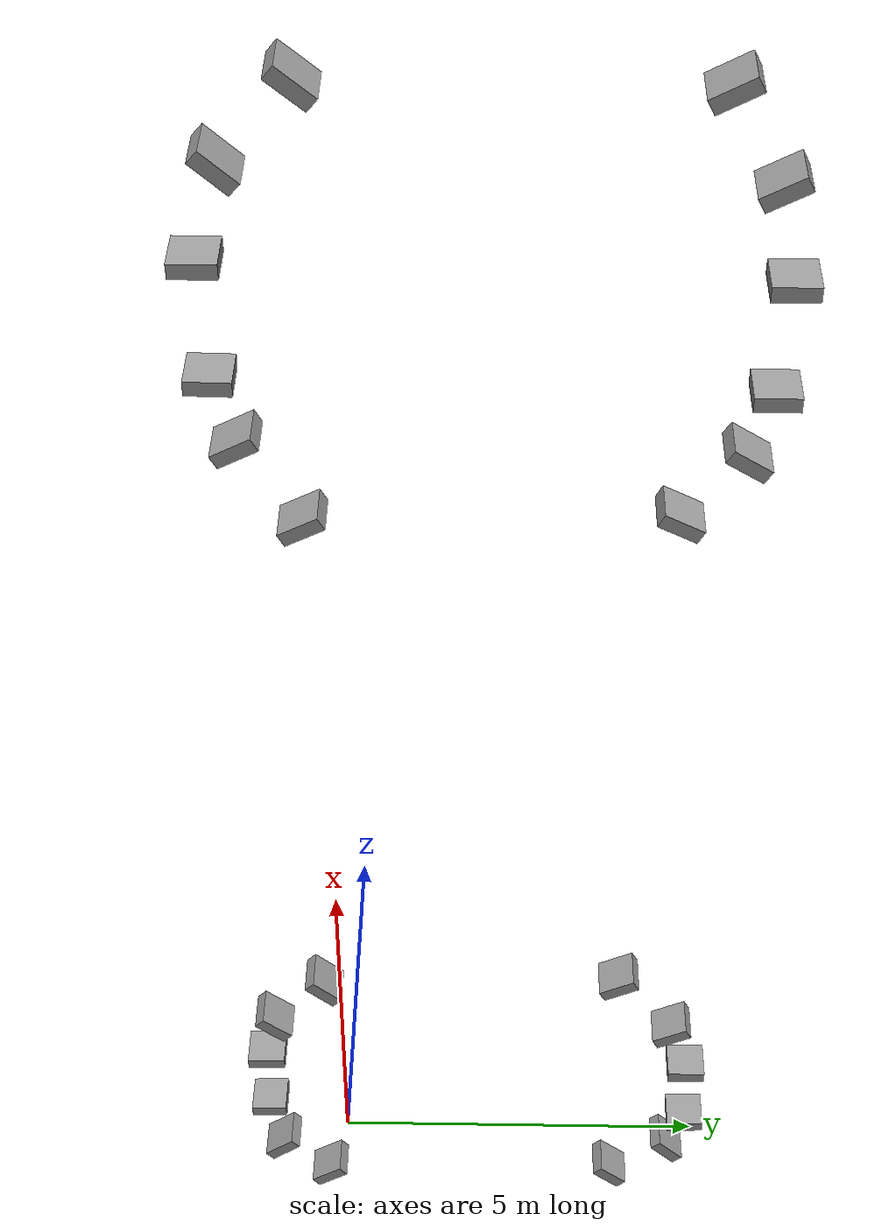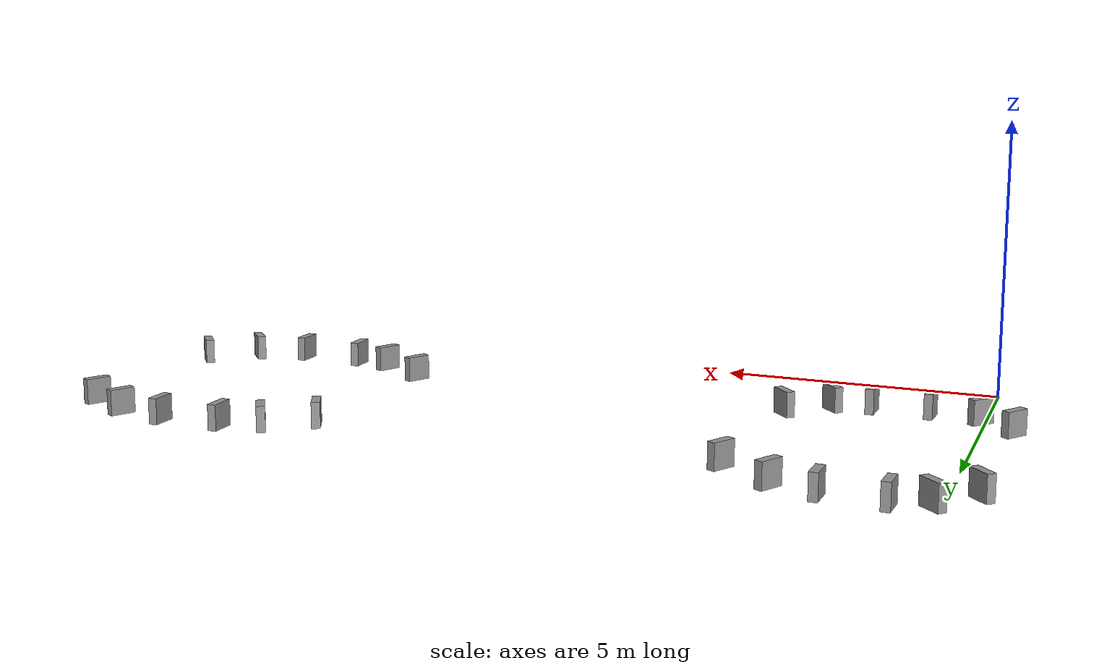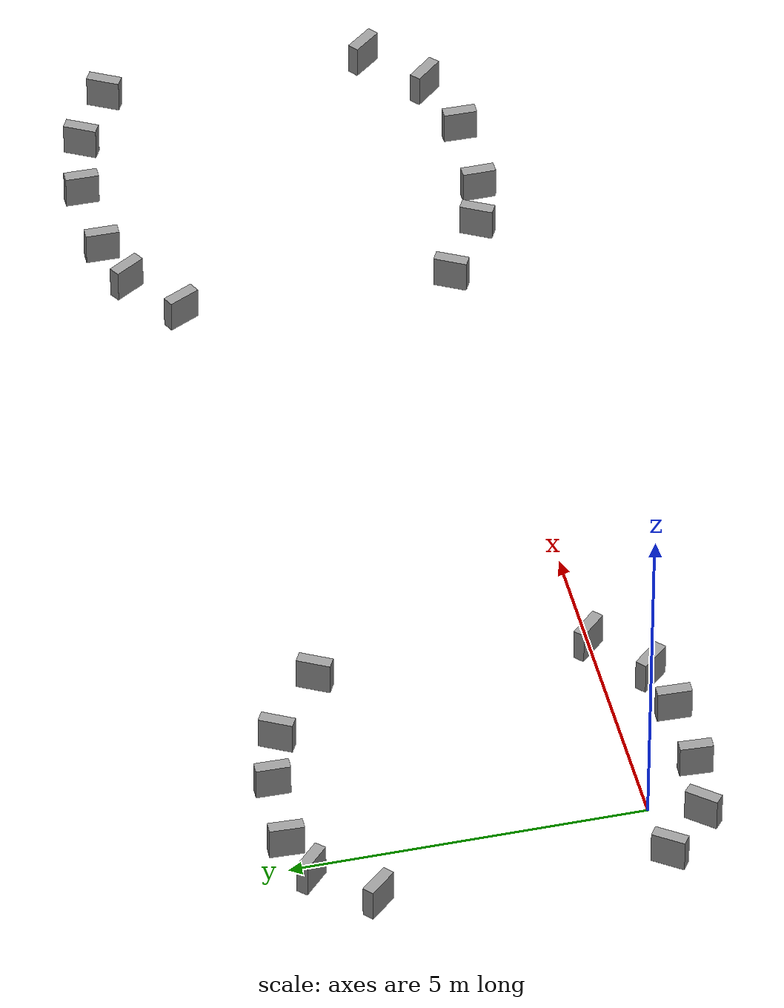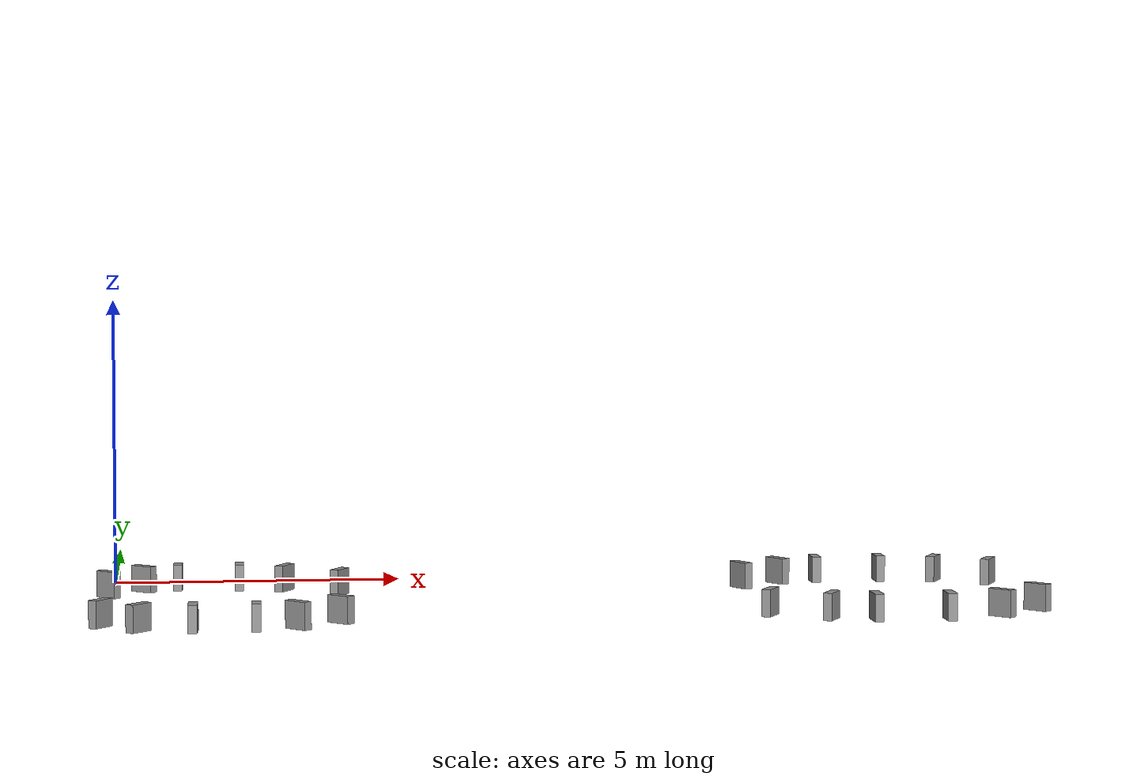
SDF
<?xml version='1.0'?>
<sdf version='1.6'>
  <model name='unit_box_0'>
    <link name='link'>
      <pose frame=''>-0.278731 -0.23831 1e-06 0 0 -0.611558</pose>
      <inertial>
        <mass>0.546277</mass>
        <inertia>
          <ixx>0.0890544</ixx>
          <ixy>0</ixy>
          <ixz>0</ixz>
          <iyy>0.0597297</iyy>
          <iyz>0</iyz>
          <izz>0.0577378</izz>
        </inertia>
        <pose frame=''>0 0 0 0 -0 0</pose>
      </inertial>
      <self_collide>0</self_collide>
      <kinematic>0</kinematic>
      <gravity>1</gravity>
      <visual name='visual'>
        <geometry>
          <box>
            <size>0.167591 0.48895 0.5</size>
          </box>
        </geometry>
        <material>
          <script>
            <name>Gazebo/Grey</name>
            <uri>file://media/materials/scripts/gazebo.material</uri>
          </script>
          <ambient>0.3 0.3 0.3 1</ambient>
          <diffuse>0.7 0.7 0.7 1</diffuse>
          <specular>0.01 0.01 0.01 1</specular>
          <emissive>0 0 0 1</emissive>
          <shader type='vertex'>
            <normal_map>__default__</normal_map>
          </shader>
        </material>
        <pose frame=''>0 0 -0.5 0 -0 0</pose>
        <cast_shadows>1</cast_shadows>
        <transparency>0</transparency>
      </visual>
      <collision name='collision'>
        <laser_retro>0</laser_retro>
        <max_contacts>10</max_contacts>
        <pose frame=''>0 0 -0.5 0 -0 0</pose>
        <geometry>
          <box>
            <size>0.167591 0.48895 0.5</size>
          </box>
        </geometry>
        <surface>
          <friction>
            <ode>
              <mu>1</mu>
              <mu2>1</mu2>
              <fdir1>0 0 0</fdir1>
              <slip1>0</slip1>
              <slip2>0</slip2>
            </ode>
            <torsional>
              <coefficient>1</coefficient>
              <patch_radius>0</patch_radius>
              <surface_radius>0</surface_radius>
              <use_patch_radius>1</use_patch_radius>
              <ode>
                <slip>0</slip>
              </ode>
            </torsional>
          </friction>
          <bounce>
            <restitution_coefficient>0</restitution_coefficient>
            <threshold>1e+06</threshold>
          </bounce>
          <contact>
            <collide_without_contact>0</collide_without_contact>
            <collide_without_contact_bitmask>1</collide_without_contact_bitmask>
            <collide_bitmask>1</collide_bitmask>
            <ode>
              <soft_cfm>0</soft_cfm>
              <soft_erp>0.2</soft_erp>
              <kp>1e+13</kp>
              <kd>1</kd>
              <max_vel>0.01</max_vel>
              <min_depth>0</min_depth>
            </ode>
            <bullet>
              <split_impulse>1</split_impulse>
              <split_impulse_penetration_threshold>-0.01</split_impulse_penetration_threshold>
              <soft_cfm>0</soft_cfm>
              <soft_erp>0.2</soft_erp>
              <kp>1e+13</kp>
              <kd>1</kd>
            </bullet>
          </contact>
        </surface>
      </collision>
    </link>
    <link name='link_clone'>
      <pose frame=''>0.390702 -0.87965 9e-06 -8e-06 -7e-06 -0.700576</pose>
      <inertial>
        <mass>0.546277</mass>
        <inertia>
          <ixx>0.0890544</ixx>
          <ixy>0</ixy>
          <ixz>0</ixz>
          <iyy>0.0597297</iyy>
          <iyz>0</iyz>
          <izz>0.0577378</izz>
        </inertia>
        <pose frame=''>0 0 0 0 -0 0</pose>
      </inertial>
      <self_collide>0</self_collide>
      <kinematic>0</kinematic>
      <gravity>1</gravity>
      <visual name='visual'>
        <geometry>
          <box>
            <size>0.167591 0.48895 0.5</size>
          </box>
        </geometry>
        <material>
          <script>
            <name>Gazebo/Grey</name>
            <uri>file://media/materials/scripts/gazebo.material</uri>
          </script>
          <ambient>0.3 0.3 0.3 1</ambient>
          <diffuse>0.7 0.7 0.7 1</diffuse>
          <specular>0.01 0.01 0.01 1</specular>
          <emissive>0 0 0 1</emissive>
          <shader type='vertex'>
            <normal_map>__default__</normal_map>
          </shader>
        </material>
        <pose frame=''>0 0 -0.5 0 -0 0</pose>
        <cast_shadows>1</cast_shadows>
        <transparency>0</transparency>
      </visual>
      <collision name='collision'>
        <laser_retro>0</laser_retro>
        <max_contacts>10</max_contacts>
        <pose frame=''>0 0 -0.5 0 -0 0</pose>
        <geometry>
          <box>
            <size>0.167591 0.48895 0.5</size>
          </box>
        </geometry>
        <surface>
          <friction>
            <ode>
              <mu>1</mu>
              <mu2>1</mu2>
              <fdir1>0 0 0</fdir1>
              <slip1>0</slip1>
              <slip2>0</slip2>
            </ode>
            <torsional>
              <coefficient>1</coefficient>
              <patch_radius>0</patch_radius>
              <surface_radius>0</surface_radius>
              <use_patch_radius>1</use_patch_radius>
              <ode>
                <slip>0</slip>
              </ode>
            </torsional>
          </friction>
          <bounce>
            <restitution_coefficient>0</restitution_coefficient>
            <threshold>1e+06</threshold>
          </bounce>
          <contact>
            <collide_without_contact>0</collide_without_contact>
            <collide_without_contact_bitmask>1</collide_without_contact_bitmask>
            <collide_bitmask>1</collide_bitmask>
            <ode>
              <soft_cfm>0</soft_cfm>
              <soft_erp>0.2</soft_erp>
              <kp>1e+13</kp>
              <kd>1</kd>
              <max_vel>0.01</max_vel>
              <min_depth>0</min_depth>
            </ode>
            <bullet>
              <split_impulse>1</split_impulse>
              <split_impulse_penetration_threshold>-0.01</split_impulse_penetration_threshold>
              <soft_cfm>0</soft_cfm>
              <soft_erp>0.2</soft_erp>
              <kp>1e+13</kp>
              <kd>1</kd>
            </bullet>
          </contact>
        </surface>
      </collision>
    </link>
    <link name='link_clone_0'>
      <pose frame=''>3.11569 4.45862 -4.4e-05 -9e-06 -5e-06 -0.493855</pose>
      <inertial>
        <mass>0.546277</mass>
        <inertia>
          <ixx>0.0890544</ixx>
          <ixy>0</ixy>
          <ixz>0</ixz>
          <iyy>0.0597297</iyy>
          <iyz>0</iyz>
          <izz>0.0577378</izz>
        </inertia>
        <pose frame=''>0 0 0 0 -0 0</pose>
      </inertial>
      <self_collide>0</self_collide>
      <kinematic>0</kinematic>
      <gravity>1</gravity>
      <visual name='visual'>
        <geometry>
          <box>
            <size>0.167591 0.48895 0.5</size>
          </box>
        </geometry>
        <material>
          <script>
            <name>Gazebo/Grey</name>
            <uri>file://media/materials/scripts/gazebo.material</uri>
          </script>
          <ambient>0.3 0.3 0.3 1</ambient>
          <diffuse>0.7 0.7 0.7 1</diffuse>
          <specular>0.01 0.01 0.01 1</specular>
          <emissive>0 0 0 1</emissive>
          <shader type='vertex'>
            <normal_map>__default__</normal_map>
          </shader>
        </material>
        <pose frame=''>0 0 -0.5 0 -0 0</pose>
        <cast_shadows>1</cast_shadows>
        <transparency>0</transparency>
      </visual>
      <collision name='collision'>
        <laser_retro>0</laser_retro>
        <max_contacts>10</max_contacts>
        <pose frame=''>0 0 -0.5 0 -0 0</pose>
        <geometry>
          <box>
            <size>0.167591 0.48895 0.5</size>
          </box>
        </geometry>
        <surface>
          <friction>
            <ode>
              <mu>1</mu>
              <mu2>1</mu2>
              <fdir1>0 0 0</fdir1>
              <slip1>0</slip1>
              <slip2>0</slip2>
            </ode>
            <torsional>
              <coefficient>1</coefficient>
              <patch_radius>0</patch_radius>
              <surface_radius>0</surface_radius>
              <use_patch_radius>1</use_patch_radius>
              <ode>
                <slip>0</slip>
              </ode>
            </torsional>
          </friction>
          <bounce>
            <restitution_coefficient>0</restitution_coefficient>
            <threshold>1e+06</threshold>
          </bounce>
          <contact>
            <collide_without_contact>0</collide_without_contact>
            <collide_without_contact_bitmask>1</collide_without_contact_bitmask>
            <collide_bitmask>1</collide_bitmask>
            <ode>
              <soft_cfm>0</soft_cfm>
              <soft_erp>0.2</soft_erp>
              <kp>1e+13</kp>
              <kd>1</kd>
              <max_vel>0.01</max_vel>
              <min_depth>0</min_depth>
            </ode>
            <bullet>
              <split_impulse>1</split_impulse>
              <split_impulse_penetration_threshold>-0.01</split_impulse_penetration_threshold>
              <soft_cfm>0</soft_cfm>
              <soft_erp>0.2</soft_erp>
              <kp>1e+13</kp>
              <kd>1</kd>
            </bullet>
          </contact>
        </surface>
      </collision>
    </link>
    <link name='link_clone_1'>
      <pose frame=''>4.13147 3.69385 -3.6e-05 -9e-06 -5e-06 -0.493855</pose>
      <inertial>
        <mass>0.546277</mass>
        <inertia>
          <ixx>0.0890544</ixx>
          <ixy>0</ixy>
          <ixz>0</ixz>
          <iyy>0.0597297</iyy>
          <iyz>0</iyz>
          <izz>0.0577378</izz>
        </inertia>
        <pose frame=''>0 0 0 0 -0 0</pose>
      </inertial>
      <self_collide>0</self_collide>
      <kinematic>0</kinematic>
      <gravity>1</gravity>
      <visual name='visual'>
        <geometry>
          <box>
            <size>0.167591 0.48895 0.5</size>
          </box>
        </geometry>
        <material>
          <script>
            <name>Gazebo/Grey</name>
            <uri>file://media/materials/scripts/gazebo.material</uri>
          </script>
          <ambient>0.3 0.3 0.3 1</ambient>
          <diffuse>0.7 0.7 0.7 1</diffuse>
          <specular>0.01 0.01 0.01 1</specular>
          <emissive>0 0 0 1</emissive>
          <shader type='vertex'>
            <normal_map>__default__</normal_map>
          </shader>
        </material>
        <pose frame=''>0 0 -0.5 0 -0 0</pose>
        <cast_shadows>1</cast_shadows>
        <transparency>0</transparency>
      </visual>
      <collision name='collision'>
        <laser_retro>0</laser_retro>
        <max_contacts>10</max_contacts>
        <pose frame=''>0 0 -0.5 0 -0 0</pose>
        <geometry>
          <box>
            <size>0.167591 0.48895 0.5</size>
          </box>
        </geometry>
        <surface>
          <friction>
            <ode>
              <mu>1</mu>
              <mu2>1</mu2>
              <fdir1>0 0 0</fdir1>
              <slip1>0</slip1>
              <slip2>0</slip2>
            </ode>
            <torsional>
              <coefficient>1</coefficient>
              <patch_radius>0</patch_radius>
              <surface_radius>0</surface_radius>
              <use_patch_radius>1</use_patch_radius>
              <ode>
                <slip>0</slip>
              </ode>
            </torsional>
          </friction>
          <bounce>
            <restitution_coefficient>0</restitution_coefficient>
            <threshold>1e+06</threshold>
          </bounce>
          <contact>
            <collide_without_contact>0</collide_without_contact>
            <collide_without_contact_bitmask>1</collide_without_contact_bitmask>
            <collide_bitmask>1</collide_bitmask>
            <ode>
              <soft_cfm>0</soft_cfm>
              <soft_erp>0.2</soft_erp>
              <kp>1e+13</kp>
              <kd>1</kd>
              <max_vel>0.01</max_vel>
              <min_depth>0</min_depth>
            </ode>
            <bullet>
              <split_impulse>1</split_impulse>
              <split_impulse_penetration_threshold>-0.01</split_impulse_penetration_threshold>
              <soft_cfm>0</soft_cfm>
              <soft_erp>0.2</soft_erp>
              <kp>1e+13</kp>
              <kd>1</kd>
            </bullet>
          </contact>
        </surface>
      </collision>
    </link>
    <link name='link_clone_10'>
      <pose frame=''>11.743 -0.072853 1e-06 -9e-06 -5e-06 -0.493855</pose>
      <inertial>
        <mass>0.546277</mass>
        <inertia>
          <ixx>0.0890544</ixx>
          <ixy>0</ixy>
          <ixz>0</ixz>
          <iyy>0.0597297</iyy>
          <iyz>0</iyz>
          <izz>0.0577378</izz>
        </inertia>
        <pose frame=''>0 0 0 0 -0 0</pose>
      </inertial>
      <self_collide>0</self_collide>
      <kinematic>0</kinematic>
      <gravity>1</gravity>
      <visual name='visual'>
        <geometry>
          <box>
            <size>0.167591 0.48895 0.5</size>
          </box>
        </geometry>
        <material>
          <script>
            <name>Gazebo/Grey</name>
            <uri>file://media/materials/scripts/gazebo.material</uri>
          </script>
          <ambient>0.3 0.3 0.3 1</ambient>
          <diffuse>0.7 0.7 0.7 1</diffuse>
          <specular>0.01 0.01 0.01 1</specular>
          <emissive>0 0 0 1</emissive>
          <shader type='vertex'>
            <normal_map>__default__</normal_map>
          </shader>
        </material>
        <pose frame=''>0 0 -0.5 0 -0 0</pose>
        <cast_shadows>1</cast_shadows>
        <transparency>0</transparency>
      </visual>
      <collision name='collision'>
        <laser_retro>0</laser_retro>
        <max_contacts>10</max_contacts>
        <pose frame=''>0 0 -0.5 0 -0 0</pose>
        <geometry>
          <box>
            <size>0.167591 0.48895 0.5</size>
          </box>
        </geometry>
        <surface>
          <friction>
            <ode>
              <mu>1</mu>
              <mu2>1</mu2>
              <fdir1>0 0 0</fdir1>
              <slip1>0</slip1>
              <slip2>0</slip2>
            </ode>
            <torsional>
              <coefficient>1</coefficient>
              <patch_radius>0</patch_radius>
              <surface_radius>0</surface_radius>
              <use_patch_radius>1</use_patch_radius>
              <ode>
                <slip>0</slip>
              </ode>
            </torsional>
          </friction>
          <bounce>
            <restitution_coefficient>0</restitution_coefficient>
            <threshold>1e+06</threshold>
          </bounce>
          <contact>
            <collide_without_contact>0</collide_without_contact>
            <collide_without_contact_bitmask>1</collide_without_contact_bitmask>
            <collide_bitmask>1</collide_bitmask>
            <ode>
              <soft_cfm>0</soft_cfm>
              <soft_erp>0.2</soft_erp>
              <kp>1e+13</kp>
              <kd>1</kd>
              <max_vel>0.01</max_vel>
              <min_depth>0</min_depth>
            </ode>
            <bullet>
              <split_impulse>1</split_impulse>
              <split_impulse_penetration_threshold>-0.01</split_impulse_penetration_threshold>
              <soft_cfm>0</soft_cfm>
              <soft_erp>0.2</soft_erp>
              <kp>1e+13</kp>
              <kd>1</kd>
            </bullet>
          </contact>
        </surface>
      </collision>
    </link>
    <link name='link_clone_11'>
      <pose frame=''>12.7478 -0.699639 7e-06 -9e-06 -5e-06 -0.493855</pose>
      <inertial>
        <mass>0.546277</mass>
        <inertia>
          <ixx>0.0890544</ixx>
          <ixy>0</ixy>
          <ixz>0</ixz>
          <iyy>0.0597297</iyy>
          <iyz>0</iyz>
          <izz>0.0577378</izz>
        </inertia>
        <pose frame=''>0 0 0 0 -0 0</pose>
      </inertial>
      <self_collide>0</self_collide>
      <kinematic>0</kinematic>
      <gravity>1</gravity>
      <visual name='visual'>
        <geometry>
          <box>
            <size>0.167591 0.48895 0.5</size>
          </box>
        </geometry>
        <material>
          <script>
            <name>Gazebo/Grey</name>
            <uri>file://media/materials/scripts/gazebo.material</uri>
          </script>
          <ambient>0.3 0.3 0.3 1</ambient>
          <diffuse>0.7 0.7 0.7 1</diffuse>
          <specular>0.01 0.01 0.01 1</specular>
          <emissive>0 0 0 1</emissive>
          <shader type='vertex'>
            <normal_map>__default__</normal_map>
          </shader>
        </material>
        <pose frame=''>0 0 -0.5 0 -0 0</pose>
        <cast_shadows>1</cast_shadows>
        <transparency>0</transparency>
      </visual>
      <collision name='collision'>
        <laser_retro>0</laser_retro>
        <max_contacts>10</max_contacts>
        <pose frame=''>0 0 -0.5 0 -0 0</pose>
        <geometry>
          <box>
            <size>0.167591 0.48895 0.5</size>
          </box>
        </geometry>
        <surface>
          <friction>
            <ode>
              <mu>1</mu>
              <mu2>1</mu2>
              <fdir1>0 0 0</fdir1>
              <slip1>0</slip1>
              <slip2>0</slip2>
            </ode>
            <torsional>
              <coefficient>1</coefficient>
              <patch_radius>0</patch_radius>
              <surface_radius>0</surface_radius>
              <use_patch_radius>1</use_patch_radius>
              <ode>
                <slip>0</slip>
              </ode>
            </torsional>
          </friction>
          <bounce>
            <restitution_coefficient>0</restitution_coefficient>
            <threshold>1e+06</threshold>
          </bounce>
          <contact>
            <collide_without_contact>0</collide_without_contact>
            <collide_without_contact_bitmask>1</collide_without_contact_bitmask>
            <collide_bitmask>1</collide_bitmask>
            <ode>
              <soft_cfm>0</soft_cfm>
              <soft_erp>0.2</soft_erp>
              <kp>1e+13</kp>
              <kd>1</kd>
              <max_vel>0.01</max_vel>
              <min_depth>0</min_depth>
            </ode>
            <bullet>
              <split_impulse>1</split_impulse>
              <split_impulse_penetration_threshold>-0.01</split_impulse_penetration_threshold>
              <soft_cfm>0</soft_cfm>
              <soft_erp>0.2</soft_erp>
              <kp>1e+13</kp>
              <kd>1</kd>
            </bullet>
          </contact>
        </surface>
      </collision>
    </link>
    <link name='link_clone_12'>
      <pose frame=''>13.5314 -0.901205 9e-06 -1e-05 -0 0.012272</pose>
      <inertial>
        <mass>0.546277</mass>
        <inertia>
          <ixx>0.0890544</ixx>
          <ixy>0</ixy>
          <ixz>0</ixz>
          <iyy>0.0597297</iyy>
          <iyz>0</iyz>
          <izz>0.0577378</izz>
        </inertia>
        <pose frame=''>0 0 0 0 -0 0</pose>
      </inertial>
      <self_collide>0</self_collide>
      <kinematic>0</kinematic>
      <gravity>1</gravity>
      <visual name='visual'>
        <geometry>
          <box>
            <size>0.167591 0.48895 0.5</size>
          </box>
        </geometry>
        <material>
          <script>
            <name>Gazebo/Grey</name>
            <uri>file://media/materials/scripts/gazebo.material</uri>
          </script>
          <ambient>0.3 0.3 0.3 1</ambient>
          <diffuse>0.7 0.7 0.7 1</diffuse>
          <specular>0.01 0.01 0.01 1</specular>
          <emissive>0 0 0 1</emissive>
          <shader type='vertex'>
            <normal_map>__default__</normal_map>
          </shader>
        </material>
        <pose frame=''>0 0 -0.5 0 -0 0</pose>
        <cast_shadows>1</cast_shadows>
        <transparency>0</transparency>
      </visual>
      <collision name='collision'>
        <laser_retro>0</laser_retro>
        <max_contacts>10</max_contacts>
        <pose frame=''>0 0 -0.5 0 -0 0</pose>
        <geometry>
          <box>
            <size>0.167591 0.48895 0.5</size>
          </box>
        </geometry>
        <surface>
          <friction>
            <ode>
              <mu>1</mu>
              <mu2>1</mu2>
              <fdir1>0 0 0</fdir1>
              <slip1>0</slip1>
              <slip2>0</slip2>
            </ode>
            <torsional>
              <coefficient>1</coefficient>
              <patch_radius>0</patch_radius>
              <surface_radius>0</surface_radius>
              <use_patch_radius>1</use_patch_radius>
              <ode>
                <slip>0</slip>
              </ode>
            </torsional>
          </friction>
          <bounce>
            <restitution_coefficient>0</restitution_coefficient>
            <threshold>1e+06</threshold>
          </bounce>
          <contact>
            <collide_without_contact>0</collide_without_contact>
            <collide_without_contact_bitmask>1</collide_without_contact_bitmask>
            <collide_bitmask>1</collide_bitmask>
            <ode>
              <soft_cfm>0</soft_cfm>
              <soft_erp>0.2</soft_erp>
              <kp>1e+13</kp>
              <kd>1</kd>
              <max_vel>0.01</max_vel>
              <min_depth>0</min_depth>
            </ode>
            <bullet>
              <split_impulse>1</split_impulse>
              <split_impulse_penetration_threshold>-0.01</split_impulse_penetration_threshold>
              <soft_cfm>0</soft_cfm>
              <soft_erp>0.2</soft_erp>
              <kp>1e+13</kp>
              <kd>1</kd>
            </bullet>
          </contact>
        </surface>
      </collision>
    </link>
    <link name='link_clone_13'>
      <pose frame=''>14.8607 -0.938747 9e-06 -1e-05 -0 -0.013351</pose>
      <inertial>
        <mass>0.546277</mass>
        <inertia>
          <ixx>0.0890544</ixx>
          <ixy>0</ixy>
          <ixz>0</ixz>
          <iyy>0.0597297</iyy>
          <iyz>0</iyz>
          <izz>0.0577378</izz>
        </inertia>
        <pose frame=''>0 0 0 0 -0 0</pose>
      </inertial>
      <self_collide>0</self_collide>
      <kinematic>0</kinematic>
      <gravity>1</gravity>
      <visual name='visual'>
        <geometry>
          <box>
            <size>0.167591 0.48895 0.5</size>
          </box>
        </geometry>
        <material>
          <script>
            <name>Gazebo/Grey</name>
            <uri>file://media/materials/scripts/gazebo.material</uri>
          </script>
          <ambient>0.3 0.3 0.3 1</ambient>
          <diffuse>0.7 0.7 0.7 1</diffuse>
          <specular>0.01 0.01 0.01 1</specular>
          <emissive>0 0 0 1</emissive>
          <shader type='vertex'>
            <normal_map>__default__</normal_map>
          </shader>
        </material>
        <pose frame=''>0 0 -0.5 0 -0 0</pose>
        <cast_shadows>1</cast_shadows>
        <transparency>0</transparency>
      </visual>
      <collision name='collision'>
        <laser_retro>0</laser_retro>
        <max_contacts>10</max_contacts>
        <pose frame=''>0 0 -0.5 0 -0 0</pose>
        <geometry>
          <box>
            <size>0.167591 0.48895 0.5</size>
          </box>
        </geometry>
        <surface>
          <friction>
            <ode>
              <mu>1</mu>
              <mu2>1</mu2>
              <fdir1>0 0 0</fdir1>
              <slip1>0</slip1>
              <slip2>0</slip2>
            </ode>
            <torsional>
              <coefficient>1</coefficient>
              <patch_radius>0</patch_radius>
              <surface_radius>0</surface_radius>
              <use_patch_radius>1</use_patch_radius>
              <ode>
                <slip>0</slip>
              </ode>
            </torsional>
          </friction>
          <bounce>
            <restitution_coefficient>0</restitution_coefficient>
            <threshold>1e+06</threshold>
          </bounce>
          <contact>
            <collide_without_contact>0</collide_without_contact>
            <collide_without_contact_bitmask>1</collide_without_contact_bitmask>
            <collide_bitmask>1</collide_bitmask>
            <ode>
              <soft_cfm>0</soft_cfm>
              <soft_erp>0.2</soft_erp>
              <kp>1e+13</kp>
              <kd>1</kd>
              <max_vel>0.01</max_vel>
              <min_depth>0</min_depth>
            </ode>
            <bullet>
              <split_impulse>1</split_impulse>
              <split_impulse_penetration_threshold>-0.01</split_impulse_penetration_threshold>
              <soft_cfm>0</soft_cfm>
              <soft_erp>0.2</soft_erp>
              <kp>1e+13</kp>
              <kd>1</kd>
            </bullet>
          </contact>
        </surface>
      </collision>
    </link>
    <link name='link_clone_14'>
      <pose frame=''>15.8877 -0.660154 6e-06 -7e-06 6e-06 0.721031</pose>
      <inertial>
        <mass>0.546277</mass>
        <inertia>
          <ixx>0.0890544</ixx>
          <ixy>0</ixy>
          <ixz>0</ixz>
          <iyy>0.0597297</iyy>
          <iyz>0</iyz>
          <izz>0.0577378</izz>
        </inertia>
        <pose frame=''>0 0 0 0 -0 0</pose>
      </inertial>
      <self_collide>0</self_collide>
      <kinematic>0</kinematic>
      <gravity>1</gravity>
      <visual name='visual'>
        <geometry>
          <box>
            <size>0.167591 0.48895 0.5</size>
          </box>
        </geometry>
        <material>
          <script>
            <name>Gazebo/Grey</name>
            <uri>file://media/materials/scripts/gazebo.material</uri>
          </script>
          <ambient>0.3 0.3 0.3 1</ambient>
          <diffuse>0.7 0.7 0.7 1</diffuse>
          <specular>0.01 0.01 0.01 1</specular>
          <emissive>0 0 0 1</emissive>
          <shader type='vertex'>
            <normal_map>__default__</normal_map>
          </shader>
        </material>
        <pose frame=''>0 0 -0.5 0 -0 0</pose>
        <cast_shadows>1</cast_shadows>
        <transparency>0</transparency>
      </visual>
      <collision name='collision'>
        <laser_retro>0</laser_retro>
        <max_contacts>10</max_contacts>
        <pose frame=''>0 0 -0.5 0 -0 0</pose>
        <geometry>
          <box>
            <size>0.167591 0.48895 0.5</size>
          </box>
        </geometry>
        <surface>
          <friction>
            <ode>
              <mu>1</mu>
              <mu2>1</mu2>
              <fdir1>0 0 0</fdir1>
              <slip1>0</slip1>
              <slip2>0</slip2>
            </ode>
            <torsional>
              <coefficient>1</coefficient>
              <patch_radius>0</patch_radius>
              <surface_radius>0</surface_radius>
              <use_patch_radius>1</use_patch_radius>
              <ode>
                <slip>0</slip>
              </ode>
            </torsional>
          </friction>
          <bounce>
            <restitution_coefficient>0</restitution_coefficient>
            <threshold>1e+06</threshold>
          </bounce>
          <contact>
            <collide_without_contact>0</collide_without_contact>
            <collide_without_contact_bitmask>1</collide_without_contact_bitmask>
            <collide_bitmask>1</collide_bitmask>
            <ode>
              <soft_cfm>0</soft_cfm>
              <soft_erp>0.2</soft_erp>
              <kp>1e+13</kp>
              <kd>1</kd>
              <max_vel>0.01</max_vel>
              <min_depth>0</min_depth>
            </ode>
            <bullet>
              <split_impulse>1</split_impulse>
              <split_impulse_penetration_threshold>-0.01</split_impulse_penetration_threshold>
              <soft_cfm>0</soft_cfm>
              <soft_erp>0.2</soft_erp>
              <kp>1e+13</kp>
              <kd>1</kd>
            </bullet>
          </contact>
        </surface>
      </collision>
    </link>
    <link name='link_clone_15'>
      <pose frame=''>16.7275 0.073517 -1e-06 -8e-06 6e-06 0.678846</pose>
      <inertial>
        <mass>0.546277</mass>
        <inertia>
          <ixx>0.0890544</ixx>
          <ixy>0</ixy>
          <ixz>0</ixz>
          <iyy>0.0597297</iyy>
          <iyz>0</iyz>
          <izz>0.0577378</izz>
        </inertia>
        <pose frame=''>0 0 -0 0 -0 0</pose>
      </inertial>
      <self_collide>0</self_collide>
      <kinematic>0</kinematic>
      <gravity>1</gravity>
      <visual name='visual'>
        <geometry>
          <box>
            <size>0.167591 0.48895 0.5</size>
          </box>
        </geometry>
        <material>
          <script>
            <name>Gazebo/Grey</name>
            <uri>file://media/materials/scripts/gazebo.material</uri>
          </script>
          <ambient>0.3 0.3 0.3 1</ambient>
          <diffuse>0.7 0.7 0.7 1</diffuse>
          <specular>0.01 0.01 0.01 1</specular>
          <emissive>0 0 0 1</emissive>
          <shader type='vertex'>
            <normal_map>__default__</normal_map>
          </shader>
        </material>
        <pose frame=''>0 0 -0.5 0 -0 0</pose>
        <cast_shadows>1</cast_shadows>
        <transparency>0</transparency>
      </visual>
      <collision name='collision'>
        <laser_retro>0</laser_retro>
        <max_contacts>10</max_contacts>
        <pose frame=''>0 0 -0.5 0 -0 0</pose>
        <geometry>
          <box>
            <size>0.167591 0.48895 0.5</size>
          </box>
        </geometry>
        <surface>
          <friction>
            <ode>
              <mu>1</mu>
              <mu2>1</mu2>
              <fdir1>0 0 0</fdir1>
              <slip1>0</slip1>
              <slip2>0</slip2>
            </ode>
            <torsional>
              <coefficient>1</coefficient>
              <patch_radius>0</patch_radius>
              <surface_radius>0</surface_radius>
              <use_patch_radius>1</use_patch_radius>
              <ode>
                <slip>0</slip>
              </ode>
            </torsional>
          </friction>
          <bounce>
            <restitution_coefficient>0</restitution_coefficient>
            <threshold>1e+06</threshold>
          </bounce>
          <contact>
            <collide_without_contact>0</collide_without_contact>
            <collide_without_contact_bitmask>1</collide_without_contact_bitmask>
            <collide_bitmask>1</collide_bitmask>
            <ode>
              <soft_cfm>0</soft_cfm>
              <soft_erp>0.2</soft_erp>
              <kp>1e+13</kp>
              <kd>1</kd>
              <max_vel>0.01</max_vel>
              <min_depth>0</min_depth>
            </ode>
            <bullet>
              <split_impulse>1</split_impulse>
              <split_impulse_penetration_threshold>-0.01</split_impulse_penetration_threshold>
              <soft_cfm>0</soft_cfm>
              <soft_erp>0.2</soft_erp>
              <kp>1e+13</kp>
              <kd>1</kd>
            </bullet>
          </contact>
        </surface>
      </collision>
    </link>
    <link name='link_clone_16'>
      <pose frame=''>11.8743 3.88781 -3.8e-05 -9e-06 4e-06 0.46484</pose>
      <inertial>
        <mass>0.546277</mass>
        <inertia>
          <ixx>0.0890544</ixx>
          <ixy>0</ixy>
          <ixz>0</ixz>
          <iyy>0.0597297</iyy>
          <iyz>0</iyz>
          <izz>0.0577378</izz>
        </inertia>
        <pose frame=''>0 0 0 0 -0 0</pose>
      </inertial>
      <self_collide>0</self_collide>
      <kinematic>0</kinematic>
      <gravity>1</gravity>
      <visual name='visual'>
        <geometry>
          <box>
            <size>0.167591 0.48895 0.5</size>
          </box>
        </geometry>
        <material>
          <script>
            <name>Gazebo/Grey</name>
            <uri>file://media/materials/scripts/gazebo.material</uri>
          </script>
          <ambient>0.3 0.3 0.3 1</ambient>
          <diffuse>0.7 0.7 0.7 1</diffuse>
          <specular>0.01 0.01 0.01 1</specular>
          <emissive>0 0 0 1</emissive>
          <shader type='vertex'>
            <normal_map>__default__</normal_map>
          </shader>
        </material>
        <pose frame=''>0 0 -0.5 0 -0 0</pose>
        <cast_shadows>1</cast_shadows>
        <transparency>0</transparency>
      </visual>
      <collision name='collision'>
        <laser_retro>0</laser_retro>
        <max_contacts>10</max_contacts>
        <pose frame=''>0 0 -0.5 0 -0 0</pose>
        <geometry>
          <box>
            <size>0.167591 0.48895 0.5</size>
          </box>
        </geometry>
        <surface>
          <friction>
            <ode>
              <mu>1</mu>
              <mu2>1</mu2>
              <fdir1>0 0 0</fdir1>
              <slip1>0</slip1>
              <slip2>0</slip2>
            </ode>
            <torsional>
              <coefficient>1</coefficient>
              <patch_radius>0</patch_radius>
              <surface_radius>0</surface_radius>
              <use_patch_radius>1</use_patch_radius>
              <ode>
                <slip>0</slip>
              </ode>
            </torsional>
          </friction>
          <bounce>
            <restitution_coefficient>0</restitution_coefficient>
            <threshold>1e+06</threshold>
          </bounce>
          <contact>
            <collide_without_contact>0</collide_without_contact>
            <collide_without_contact_bitmask>1</collide_without_contact_bitmask>
            <collide_bitmask>1</collide_bitmask>
            <ode>
              <soft_cfm>0</soft_cfm>
              <soft_erp>0.2</soft_erp>
              <kp>1e+13</kp>
              <kd>1</kd>
              <max_vel>0.01</max_vel>
              <min_depth>0</min_depth>
            </ode>
            <bullet>
              <split_impulse>1</split_impulse>
              <split_impulse_penetration_threshold>-0.01</split_impulse_penetration_threshold>
              <soft_cfm>0</soft_cfm>
              <soft_erp>0.2</soft_erp>
              <kp>1e+13</kp>
              <kd>1</kd>
            </bullet>
          </contact>
        </surface>
      </collision>
    </link>
    <link name='link_clone_17'>
      <pose frame=''>12.6926 4.51321 -4.5e-05 -8e-06 5e-06 0.548788</pose>
      <inertial>
        <mass>0.546277</mass>
        <inertia>
          <ixx>0.0890544</ixx>
          <ixy>0</ixy>
          <ixz>0</ixz>
          <iyy>0.0597297</iyy>
          <iyz>0</iyz>
          <izz>0.0577378</izz>
        </inertia>
        <pose frame=''>0 0 0 0 -0 0</pose>
      </inertial>
      <self_collide>0</self_collide>
      <kinematic>0</kinematic>
      <gravity>1</gravity>
      <visual name='visual'>
        <geometry>
          <box>
            <size>0.167591 0.48895 0.5</size>
          </box>
        </geometry>
        <material>
          <script>
            <name>Gazebo/Grey</name>
            <uri>file://media/materials/scripts/gazebo.material</uri>
          </script>
          <ambient>0.3 0.3 0.3 1</ambient>
          <diffuse>0.7 0.7 0.7 1</diffuse>
          <specular>0.01 0.01 0.01 1</specular>
          <emissive>0 0 0 1</emissive>
          <shader type='vertex'>
            <normal_map>__default__</normal_map>
          </shader>
        </material>
        <pose frame=''>0 0 -0.5 0 -0 0</pose>
        <cast_shadows>1</cast_shadows>
        <transparency>0</transparency>
      </visual>
      <collision name='collision'>
        <laser_retro>0</laser_retro>
        <max_contacts>10</max_contacts>
        <pose frame=''>0 0 -0.5 0 -0 0</pose>
        <geometry>
          <box>
            <size>0.167591 0.48895 0.5</size>
          </box>
        </geometry>
        <surface>
          <friction>
            <ode>
              <mu>1</mu>
              <mu2>1</mu2>
              <fdir1>0 0 0</fdir1>
              <slip1>0</slip1>
              <slip2>0</slip2>
            </ode>
            <torsional>
              <coefficient>1</coefficient>
              <patch_radius>0</patch_radius>
              <surface_radius>0</surface_radius>
              <use_patch_radius>1</use_patch_radius>
              <ode>
                <slip>0</slip>
              </ode>
            </torsional>
          </friction>
          <bounce>
            <restitution_coefficient>0</restitution_coefficient>
            <threshold>1e+06</threshold>
          </bounce>
          <contact>
            <collide_without_contact>0</collide_without_contact>
            <collide_without_contact_bitmask>1</collide_without_contact_bitmask>
            <collide_bitmask>1</collide_bitmask>
            <ode>
              <soft_cfm>0</soft_cfm>
              <soft_erp>0.2</soft_erp>
              <kp>1e+13</kp>
              <kd>1</kd>
              <max_vel>0.01</max_vel>
              <min_depth>0</min_depth>
            </ode>
            <bullet>
              <split_impulse>1</split_impulse>
              <split_impulse_penetration_threshold>-0.01</split_impulse_penetration_threshold>
              <soft_cfm>0</soft_cfm>
              <soft_erp>0.2</soft_erp>
              <kp>1e+13</kp>
              <kd>1</kd>
            </bullet>
          </contact>
        </surface>
      </collision>
    </link>
    <link name='link_clone_18'>
      <pose frame=''>13.4663 4.71445 -4.6e-05 -1e-05 -0 -0.005007</pose>
      <inertial>
        <mass>0.546277</mass>
        <inertia>
          <ixx>0.0890544</ixx>
          <ixy>0</ixy>
          <ixz>0</ixz>
          <iyy>0.0597297</iyy>
          <iyz>0</iyz>
          <izz>0.0577378</izz>
        </inertia>
        <pose frame=''>0 0 0 0 -0 0</pose>
      </inertial>
      <self_collide>0</self_collide>
      <kinematic>0</kinematic>
      <gravity>1</gravity>
      <visual name='visual'>
        <geometry>
          <box>
            <size>0.167591 0.48895 0.5</size>
          </box>
        </geometry>
        <material>
          <script>
            <name>Gazebo/Grey</name>
            <uri>file://media/materials/scripts/gazebo.material</uri>
          </script>
          <ambient>0.3 0.3 0.3 1</ambient>
          <diffuse>0.7 0.7 0.7 1</diffuse>
          <specular>0.01 0.01 0.01 1</specular>
          <emissive>0 0 0 1</emissive>
          <shader type='vertex'>
            <normal_map>__default__</normal_map>
          </shader>
        </material>
        <pose frame=''>0 0 -0.5 0 -0 0</pose>
        <cast_shadows>1</cast_shadows>
        <transparency>0</transparency>
      </visual>
      <collision name='collision'>
        <laser_retro>0</laser_retro>
        <max_contacts>10</max_contacts>
        <pose frame=''>0 0 -0.5 0 -0 0</pose>
        <geometry>
          <box>
            <size>0.167591 0.48895 0.5</size>
          </box>
        </geometry>
        <surface>
          <friction>
            <ode>
              <mu>1</mu>
              <mu2>1</mu2>
              <fdir1>0 0 0</fdir1>
              <slip1>0</slip1>
              <slip2>0</slip2>
            </ode>
            <torsional>
              <coefficient>1</coefficient>
              <patch_radius>0</patch_radius>
              <surface_radius>0</surface_radius>
              <use_patch_radius>1</use_patch_radius>
              <ode>
                <slip>0</slip>
              </ode>
            </torsional>
          </friction>
          <bounce>
            <restitution_coefficient>0</restitution_coefficient>
            <threshold>1e+06</threshold>
          </bounce>
          <contact>
            <collide_without_contact>0</collide_without_contact>
            <collide_without_contact_bitmask>1</collide_without_contact_bitmask>
            <collide_bitmask>1</collide_bitmask>
            <ode>
              <soft_cfm>0</soft_cfm>
              <soft_erp>0.2</soft_erp>
              <kp>1e+13</kp>
              <kd>1</kd>
              <max_vel>0.01</max_vel>
              <min_depth>0</min_depth>
            </ode>
            <bullet>
              <split_impulse>1</split_impulse>
              <split_impulse_penetration_threshold>-0.01</split_impulse_penetration_threshold>
              <soft_cfm>0</soft_cfm>
              <soft_erp>0.2</soft_erp>
              <kp>1e+13</kp>
              <kd>1</kd>
            </bullet>
          </contact>
        </surface>
      </collision>
    </link>
    <link name='link_clone_19'>
      <pose frame=''>14.7363 4.74732 -4.7e-05 -1e-05 -0 -0.012126</pose>
      <inertial>
        <mass>0.546277</mass>
        <inertia>
          <ixx>0.0890544</ixx>
          <ixy>0</ixy>
          <ixz>0</ixz>
          <iyy>0.0597297</iyy>
          <iyz>0</iyz>
          <izz>0.0577378</izz>
        </inertia>
        <pose frame=''>0 0 0 0 -0 0</pose>
      </inertial>
      <self_collide>0</self_collide>
      <kinematic>0</kinematic>
      <gravity>1</gravity>
      <visual name='visual'>
        <geometry>
          <box>
            <size>0.167591 0.48895 0.5</size>
          </box>
        </geometry>
        <material>
          <script>
            <name>Gazebo/Grey</name>
            <uri>file://media/materials/scripts/gazebo.material</uri>
          </script>
          <ambient>0.3 0.3 0.3 1</ambient>
          <diffuse>0.7 0.7 0.7 1</diffuse>
          <specular>0.01 0.01 0.01 1</specular>
          <emissive>0 0 0 1</emissive>
          <shader type='vertex'>
            <normal_map>__default__</normal_map>
          </shader>
        </material>
        <pose frame=''>0 0 -0.5 0 -0 0</pose>
        <cast_shadows>1</cast_shadows>
        <transparency>0</transparency>
      </visual>
      <collision name='collision'>
        <laser_retro>0</laser_retro>
        <max_contacts>10</max_contacts>
        <pose frame=''>0 0 -0.5 0 -0 0</pose>
        <geometry>
          <box>
            <size>0.167591 0.48895 0.5</size>
          </box>
        </geometry>
        <surface>
          <friction>
            <ode>
              <mu>1</mu>
              <mu2>1</mu2>
              <fdir1>0 0 0</fdir1>
              <slip1>0</slip1>
              <slip2>0</slip2>
            </ode>
            <torsional>
              <coefficient>1</coefficient>
              <patch_radius>0</patch_radius>
              <surface_radius>0</surface_radius>
              <use_patch_radius>1</use_patch_radius>
              <ode>
                <slip>0</slip>
              </ode>
            </torsional>
          </friction>
          <bounce>
            <restitution_coefficient>0</restitution_coefficient>
            <threshold>1e+06</threshold>
          </bounce>
          <contact>
            <collide_without_contact>0</collide_without_contact>
            <collide_without_contact_bitmask>1</collide_without_contact_bitmask>
            <collide_bitmask>1</collide_bitmask>
            <ode>
              <soft_cfm>0</soft_cfm>
              <soft_erp>0.2</soft_erp>
              <kp>1e+13</kp>
              <kd>1</kd>
              <max_vel>0.01</max_vel>
              <min_depth>0</min_depth>
            </ode>
            <bullet>
              <split_impulse>1</split_impulse>
              <split_impulse_penetration_threshold>-0.01</split_impulse_penetration_threshold>
              <soft_cfm>0</soft_cfm>
              <soft_erp>0.2</soft_erp>
              <kp>1e+13</kp>
              <kd>1</kd>
            </bullet>
          </contact>
        </surface>
      </collision>
    </link>
    <link name='link_clone_2'>
      <pose frame=''>1.33891 -1.01246 1e-05 -1e-05 -1e-06 -0.053479</pose>
      <inertial>
        <mass>0.522552</mass>
        <inertia>
          <ixx>0.0816483</ixx>
          <ixy>0</ixy>
          <ixz>0</ixz>
          <iyy>0.0571356</iyy>
          <iyz>0</iyz>
          <izz>0.0516918</izz>
        </inertia>
        <pose frame=''>0 0 0 0 -0 0</pose>
      </inertial>
      <self_collide>0</self_collide>
      <kinematic>0</kinematic>
      <gravity>1</gravity>
      <visual name='visual'>
        <geometry>
          <box>
            <size>0.167591 0.467728 0.5</size>
          </box>
        </geometry>
        <material>
          <script>
            <name>Gazebo/Grey</name>
            <uri>file://media/materials/scripts/gazebo.material</uri>
          </script>
          <ambient>0.3 0.3 0.3 1</ambient>
          <diffuse>0.7 0.7 0.7 1</diffuse>
          <specular>0.01 0.01 0.01 1</specular>
          <emissive>0 0 0 1</emissive>
          <shader type='vertex'>
            <normal_map>__default__</normal_map>
          </shader>
        </material>
        <pose frame=''>0 0 -0.5 0 -0 0</pose>
        <cast_shadows>1</cast_shadows>
        <transparency>0</transparency>
      </visual>
      <collision name='collision'>
        <laser_retro>0</laser_retro>
        <max_contacts>10</max_contacts>
        <pose frame=''>0 0 -0.5 0 -0 0</pose>
        <geometry>
          <box>
            <size>0.167591 0.467728 0.5</size>
          </box>
        </geometry>
        <surface>
          <friction>
            <ode>
              <mu>1</mu>
              <mu2>1</mu2>
              <fdir1>0 0 0</fdir1>
              <slip1>0</slip1>
              <slip2>0</slip2>
            </ode>
            <torsional>
              <coefficient>1</coefficient>
              <patch_radius>0</patch_radius>
              <surface_radius>0</surface_radius>
              <use_patch_radius>1</use_patch_radius>
              <ode>
                <slip>0</slip>
              </ode>
            </torsional>
          </friction>
          <bounce>
            <restitution_coefficient>0</restitution_coefficient>
            <threshold>1e+06</threshold>
          </bounce>
          <contact>
            <collide_without_contact>0</collide_without_contact>
            <collide_without_contact_bitmask>1</collide_without_contact_bitmask>
            <collide_bitmask>1</collide_bitmask>
            <ode>
              <soft_cfm>0</soft_cfm>
              <soft_erp>0.2</soft_erp>
              <kp>1e+13</kp>
              <kd>1</kd>
              <max_vel>0.01</max_vel>
              <min_depth>0</min_depth>
            </ode>
            <bullet>
              <split_impulse>1</split_impulse>
              <split_impulse_penetration_threshold>-0.01</split_impulse_penetration_threshold>
              <soft_cfm>0</soft_cfm>
              <soft_erp>0.2</soft_erp>
              <kp>1e+13</kp>
              <kd>1</kd>
            </bullet>
          </contact>
        </surface>
      </collision>
    </link>
    <link name='link_clone_20'>
      <pose frame=''>15.7861 4.52739 -4.4e-05 -9e-06 -5e-06 -0.493855</pose>
      <inertial>
        <mass>0.546277</mass>
        <inertia>
          <ixx>0.0890544</ixx>
          <ixy>0</ixy>
          <ixz>0</ixz>
          <iyy>0.0597297</iyy>
          <iyz>0</iyz>
          <izz>0.0577378</izz>
        </inertia>
        <pose frame=''>0 0 0 0 -0 0</pose>
      </inertial>
      <self_collide>0</self_collide>
      <kinematic>0</kinematic>
      <gravity>1</gravity>
      <visual name='visual'>
        <geometry>
          <box>
            <size>0.167591 0.48895 0.5</size>
          </box>
        </geometry>
        <material>
          <script>
            <name>Gazebo/Grey</name>
            <uri>file://media/materials/scripts/gazebo.material</uri>
          </script>
          <ambient>0.3 0.3 0.3 1</ambient>
          <diffuse>0.7 0.7 0.7 1</diffuse>
          <specular>0.01 0.01 0.01 1</specular>
          <emissive>0 0 0 1</emissive>
          <shader type='vertex'>
            <normal_map>__default__</normal_map>
          </shader>
        </material>
        <pose frame=''>0 0 -0.5 0 -0 0</pose>
        <cast_shadows>1</cast_shadows>
        <transparency>0</transparency>
      </visual>
      <collision name='collision'>
        <laser_retro>0</laser_retro>
        <max_contacts>10</max_contacts>
        <pose frame=''>0 0 -0.5 0 -0 0</pose>
        <geometry>
          <box>
            <size>0.167591 0.48895 0.5</size>
          </box>
        </geometry>
        <surface>
          <friction>
            <ode>
              <mu>1</mu>
              <mu2>1</mu2>
              <fdir1>0 0 0</fdir1>
              <slip1>0</slip1>
              <slip2>0</slip2>
            </ode>
            <torsional>
              <coefficient>1</coefficient>
              <patch_radius>0</patch_radius>
              <surface_radius>0</surface_radius>
              <use_patch_radius>1</use_patch_radius>
              <ode>
                <slip>0</slip>
              </ode>
            </torsional>
          </friction>
          <bounce>
            <restitution_coefficient>0</restitution_coefficient>
            <threshold>1e+06</threshold>
          </bounce>
          <contact>
            <collide_without_contact>0</collide_without_contact>
            <collide_without_contact_bitmask>1</collide_without_contact_bitmask>
            <collide_bitmask>1</collide_bitmask>
            <ode>
              <soft_cfm>0</soft_cfm>
              <soft_erp>0.2</soft_erp>
              <kp>1e+13</kp>
              <kd>1</kd>
              <max_vel>0.01</max_vel>
              <min_depth>0</min_depth>
            </ode>
            <bullet>
              <split_impulse>1</split_impulse>
              <split_impulse_penetration_threshold>-0.01</split_impulse_penetration_threshold>
              <soft_cfm>0</soft_cfm>
              <soft_erp>0.2</soft_erp>
              <kp>1e+13</kp>
              <kd>1</kd>
            </bullet>
          </contact>
        </surface>
      </collision>
    </link>
    <link name='link_clone_21'>
      <pose frame=''>16.7464 3.97909 -3.9e-05 -9e-06 -5e-06 -0.493855</pose>
      <inertial>
        <mass>0.546277</mass>
        <inertia>
          <ixx>0.0890544</ixx>
          <ixy>0</ixy>
          <ixz>0</ixz>
          <iyy>0.0597297</iyy>
          <iyz>0</iyz>
          <izz>0.0577378</izz>
        </inertia>
        <pose frame=''>0 0 0 0 -0 0</pose>
      </inertial>
      <self_collide>0</self_collide>
      <kinematic>0</kinematic>
      <gravity>1</gravity>
      <visual name='visual'>
        <geometry>
          <box>
            <size>0.167591 0.48895 0.5</size>
          </box>
        </geometry>
        <material>
          <script>
            <name>Gazebo/Grey</name>
            <uri>file://media/materials/scripts/gazebo.material</uri>
          </script>
          <ambient>0.3 0.3 0.3 1</ambient>
          <diffuse>0.7 0.7 0.7 1</diffuse>
          <specular>0.01 0.01 0.01 1</specular>
          <emissive>0 0 0 1</emissive>
          <shader type='vertex'>
            <normal_map>__default__</normal_map>
          </shader>
        </material>
        <pose frame=''>0 0 -0.5 0 -0 0</pose>
        <cast_shadows>1</cast_shadows>
        <transparency>0</transparency>
      </visual>
      <collision name='collision'>
        <laser_retro>0</laser_retro>
        <max_contacts>10</max_contacts>
        <pose frame=''>0 0 -0.5 0 -0 0</pose>
        <geometry>
          <box>
            <size>0.167591 0.48895 0.5</size>
          </box>
        </geometry>
        <surface>
          <friction>
            <ode>
              <mu>1</mu>
              <mu2>1</mu2>
              <fdir1>0 0 0</fdir1>
              <slip1>0</slip1>
              <slip2>0</slip2>
            </ode>
            <torsional>
              <coefficient>1</coefficient>
              <patch_radius>0</patch_radius>
              <surface_radius>0</surface_radius>
              <use_patch_radius>1</use_patch_radius>
              <ode>
                <slip>0</slip>
              </ode>
            </torsional>
          </friction>
          <bounce>
            <restitution_coefficient>0</restitution_coefficient>
            <threshold>1e+06</threshold>
          </bounce>
          <contact>
            <collide_without_contact>0</collide_without_contact>
            <collide_without_contact_bitmask>1</collide_without_contact_bitmask>
            <collide_bitmask>1</collide_bitmask>
            <ode>
              <soft_cfm>0</soft_cfm>
              <soft_erp>0.2</soft_erp>
              <kp>1e+13</kp>
              <kd>1</kd>
              <max_vel>0.01</max_vel>
              <min_depth>0</min_depth>
            </ode>
            <bullet>
              <split_impulse>1</split_impulse>
              <split_impulse_penetration_threshold>-0.01</split_impulse_penetration_threshold>
              <soft_cfm>0</soft_cfm>
              <soft_erp>0.2</soft_erp>
              <kp>1e+13</kp>
              <kd>1</kd>
            </bullet>
          </contact>
        </surface>
      </collision>
    </link>
    <link name='link_clone_3'>
      <pose frame=''>2.44548 -0.988382 1e-05 -1e-05 -0 -0.028831</pose>
      <inertial>
        <mass>0.546277</mass>
        <inertia>
          <ixx>0.0890544</ixx>
          <ixy>0</ixy>
          <ixz>0</ixz>
          <iyy>0.0597297</iyy>
          <iyz>0</iyz>
          <izz>0.0577378</izz>
        </inertia>
        <pose frame=''>0 0 0 0 -0 0</pose>
      </inertial>
      <self_collide>0</self_collide>
      <kinematic>0</kinematic>
      <gravity>1</gravity>
      <visual name='visual'>
        <geometry>
          <box>
            <size>0.167591 0.48895 0.5</size>
          </box>
        </geometry>
        <material>
          <script>
            <name>Gazebo/Grey</name>
            <uri>file://media/materials/scripts/gazebo.material</uri>
          </script>
          <ambient>0.3 0.3 0.3 1</ambient>
          <diffuse>0.7 0.7 0.7 1</diffuse>
          <specular>0.01 0.01 0.01 1</specular>
          <emissive>0 0 0 1</emissive>
          <shader type='vertex'>
            <normal_map>__default__</normal_map>
          </shader>
        </material>
        <pose frame=''>0 0 -0.5 0 -0 0</pose>
        <cast_shadows>1</cast_shadows>
        <transparency>0</transparency>
      </visual>
      <collision name='collision'>
        <laser_retro>0</laser_retro>
        <max_contacts>10</max_contacts>
        <pose frame=''>0 0 -0.5 0 -0 0</pose>
        <geometry>
          <box>
            <size>0.167591 0.48895 0.5</size>
          </box>
        </geometry>
        <surface>
          <friction>
            <ode>
              <mu>1</mu>
              <mu2>1</mu2>
              <fdir1>0 0 0</fdir1>
              <slip1>0</slip1>
              <slip2>0</slip2>
            </ode>
            <torsional>
              <coefficient>1</coefficient>
              <patch_radius>0</patch_radius>
              <surface_radius>0</surface_radius>
              <use_patch_radius>1</use_patch_radius>
              <ode>
                <slip>0</slip>
              </ode>
            </torsional>
          </friction>
          <bounce>
            <restitution_coefficient>0</restitution_coefficient>
            <threshold>1e+06</threshold>
          </bounce>
          <contact>
            <collide_without_contact>0</collide_without_contact>
            <collide_without_contact_bitmask>1</collide_without_contact_bitmask>
            <collide_bitmask>1</collide_bitmask>
            <ode>
              <soft_cfm>0</soft_cfm>
              <soft_erp>0.2</soft_erp>
              <kp>1e+13</kp>
              <kd>1</kd>
              <max_vel>0.01</max_vel>
              <min_depth>0</min_depth>
            </ode>
            <bullet>
              <split_impulse>1</split_impulse>
              <split_impulse_penetration_threshold>-0.01</split_impulse_penetration_threshold>
              <soft_cfm>0</soft_cfm>
              <soft_erp>0.2</soft_erp>
              <kp>1e+13</kp>
              <kd>1</kd>
            </bullet>
          </contact>
        </surface>
      </collision>
    </link>
    <link name='link_clone_4'>
      <pose frame=''>3.18207 -0.849422 8e-06 -7e-06 6e-06 0.719578</pose>
      <inertial>
        <mass>0.546277</mass>
        <inertia>
          <ixx>0.0890544</ixx>
          <ixy>0</ixy>
          <ixz>0</ixz>
          <iyy>0.0597297</iyy>
          <iyz>0</iyz>
          <izz>0.0577378</izz>
        </inertia>
        <pose frame=''>0 0 0 0 -0 0</pose>
      </inertial>
      <self_collide>0</self_collide>
      <kinematic>0</kinematic>
      <gravity>1</gravity>
      <visual name='visual'>
        <geometry>
          <box>
            <size>0.167591 0.48895 0.5</size>
          </box>
        </geometry>
        <material>
          <script>
            <name>Gazebo/Grey</name>
            <uri>file://media/materials/scripts/gazebo.material</uri>
          </script>
          <ambient>0.3 0.3 0.3 1</ambient>
          <diffuse>0.7 0.7 0.7 1</diffuse>
          <specular>0.01 0.01 0.01 1</specular>
          <emissive>0 0 0 1</emissive>
          <shader type='vertex'>
            <normal_map>__default__</normal_map>
          </shader>
        </material>
        <pose frame=''>0 0 -0.5 0 -0 0</pose>
        <cast_shadows>1</cast_shadows>
        <transparency>0</transparency>
      </visual>
      <collision name='collision'>
        <laser_retro>0</laser_retro>
        <max_contacts>10</max_contacts>
        <pose frame=''>0 0 -0.5 0 -0 0</pose>
        <geometry>
          <box>
            <size>0.167591 0.48895 0.5</size>
          </box>
        </geometry>
        <surface>
          <friction>
            <ode>
              <mu>1</mu>
              <mu2>1</mu2>
              <fdir1>0 0 0</fdir1>
              <slip1>0</slip1>
              <slip2>0</slip2>
            </ode>
            <torsional>
              <coefficient>1</coefficient>
              <patch_radius>0</patch_radius>
              <surface_radius>0</surface_radius>
              <use_patch_radius>1</use_patch_radius>
              <ode>
                <slip>0</slip>
              </ode>
            </torsional>
          </friction>
          <bounce>
            <restitution_coefficient>0</restitution_coefficient>
            <threshold>1e+06</threshold>
          </bounce>
          <contact>
            <collide_without_contact>0</collide_without_contact>
            <collide_without_contact_bitmask>1</collide_without_contact_bitmask>
            <collide_bitmask>1</collide_bitmask>
            <ode>
              <soft_cfm>0</soft_cfm>
              <soft_erp>0.2</soft_erp>
              <kp>1e+13</kp>
              <kd>1</kd>
              <max_vel>0.01</max_vel>
              <min_depth>0</min_depth>
            </ode>
            <bullet>
              <split_impulse>1</split_impulse>
              <split_impulse_penetration_threshold>-0.01</split_impulse_penetration_threshold>
              <soft_cfm>0</soft_cfm>
              <soft_erp>0.2</soft_erp>
              <kp>1e+13</kp>
              <kd>1</kd>
            </bullet>
          </contact>
        </surface>
      </collision>
    </link>
    <link name='link_clone_5'>
      <pose frame=''>3.9664 -0.158271 2e-06 -7e-06 7e-06 0.761284</pose>
      <inertial>
        <mass>0.546277</mass>
        <inertia>
          <ixx>0.0890544</ixx>
          <ixy>0</ixy>
          <ixz>0</ixz>
          <iyy>0.0597297</iyy>
          <iyz>0</iyz>
          <izz>0.0577378</izz>
        </inertia>
        <pose frame=''>0 0 0 0 -0 0</pose>
      </inertial>
      <self_collide>0</self_collide>
      <kinematic>0</kinematic>
      <gravity>1</gravity>
      <visual name='visual'>
        <geometry>
          <box>
            <size>0.167591 0.48895 0.5</size>
          </box>
        </geometry>
        <material>
          <script>
            <name>Gazebo/Grey</name>
            <uri>file://media/materials/scripts/gazebo.material</uri>
          </script>
          <ambient>0.3 0.3 0.3 1</ambient>
          <diffuse>0.7 0.7 0.7 1</diffuse>
          <specular>0.01 0.01 0.01 1</specular>
          <emissive>0 0 0 1</emissive>
          <shader type='vertex'>
            <normal_map>__default__</normal_map>
          </shader>
        </material>
        <pose frame=''>0 0 -0.5 0 -0 0</pose>
        <cast_shadows>1</cast_shadows>
        <transparency>0</transparency>
      </visual>
      <collision name='collision'>
        <laser_retro>0</laser_retro>
        <max_contacts>10</max_contacts>
        <pose frame=''>0 0 -0.5 0 -0 0</pose>
        <geometry>
          <box>
            <size>0.167591 0.48895 0.5</size>
          </box>
        </geometry>
        <surface>
          <friction>
            <ode>
              <mu>1</mu>
              <mu2>1</mu2>
              <fdir1>0 0 0</fdir1>
              <slip1>0</slip1>
              <slip2>0</slip2>
            </ode>
            <torsional>
              <coefficient>1</coefficient>
              <patch_radius>0</patch_radius>
              <surface_radius>0</surface_radius>
              <use_patch_radius>1</use_patch_radius>
              <ode>
                <slip>0</slip>
              </ode>
            </torsional>
          </friction>
          <bounce>
            <restitution_coefficient>0</restitution_coefficient>
            <threshold>1e+06</threshold>
          </bounce>
          <contact>
            <collide_without_contact>0</collide_without_contact>
            <collide_without_contact_bitmask>1</collide_without_contact_bitmask>
            <collide_bitmask>1</collide_bitmask>
            <ode>
              <soft_cfm>0</soft_cfm>
              <soft_erp>0.2</soft_erp>
              <kp>1e+13</kp>
              <kd>1</kd>
              <max_vel>0.01</max_vel>
              <min_depth>0</min_depth>
            </ode>
            <bullet>
              <split_impulse>1</split_impulse>
              <split_impulse_penetration_threshold>-0.01</split_impulse_penetration_threshold>
              <soft_cfm>0</soft_cfm>
              <soft_erp>0.2</soft_erp>
              <kp>1e+13</kp>
              <kd>1</kd>
            </bullet>
          </contact>
        </surface>
      </collision>
    </link>
    <link name='link_clone_6'>
      <pose frame=''>2.2585 4.718 -4.6e-05 -1e-05 0 -0.018097</pose>
      <inertial>
        <mass>0.546277</mass>
        <inertia>
          <ixx>0.0890544</ixx>
          <ixy>0</ixy>
          <ixz>0</ixz>
          <iyy>0.0597297</iyy>
          <iyz>0</iyz>
          <izz>0.0577378</izz>
        </inertia>
        <pose frame=''>0 0 0 0 -0 0</pose>
      </inertial>
      <self_collide>0</self_collide>
      <kinematic>0</kinematic>
      <gravity>1</gravity>
      <visual name='visual'>
        <geometry>
          <box>
            <size>0.167591 0.48895 0.5</size>
          </box>
        </geometry>
        <material>
          <script>
            <name>Gazebo/Grey</name>
            <uri>file://media/materials/scripts/gazebo.material</uri>
          </script>
          <ambient>0.3 0.3 0.3 1</ambient>
          <diffuse>0.7 0.7 0.7 1</diffuse>
          <specular>0.01 0.01 0.01 1</specular>
          <emissive>0 0 0 1</emissive>
          <shader type='vertex'>
            <normal_map>__default__</normal_map>
          </shader>
        </material>
        <pose frame=''>0 0 -0.5 0 -0 0</pose>
        <cast_shadows>1</cast_shadows>
        <transparency>0</transparency>
      </visual>
      <collision name='collision'>
        <laser_retro>0</laser_retro>
        <max_contacts>10</max_contacts>
        <pose frame=''>0 0 -0.5 0 -0 0</pose>
        <geometry>
          <box>
            <size>0.167591 0.48895 0.5</size>
          </box>
        </geometry>
        <surface>
          <friction>
            <ode>
              <mu>1</mu>
              <mu2>1</mu2>
              <fdir1>0 0 0</fdir1>
              <slip1>0</slip1>
              <slip2>0</slip2>
            </ode>
            <torsional>
              <coefficient>1</coefficient>
              <patch_radius>0</patch_radius>
              <surface_radius>0</surface_radius>
              <use_patch_radius>1</use_patch_radius>
              <ode>
                <slip>0</slip>
              </ode>
            </torsional>
          </friction>
          <bounce>
            <restitution_coefficient>0</restitution_coefficient>
            <threshold>1e+06</threshold>
          </bounce>
          <contact>
            <collide_without_contact>0</collide_without_contact>
            <collide_without_contact_bitmask>1</collide_without_contact_bitmask>
            <collide_bitmask>1</collide_bitmask>
            <ode>
              <soft_cfm>0</soft_cfm>
              <soft_erp>0.2</soft_erp>
              <kp>1e+13</kp>
              <kd>1</kd>
              <max_vel>0.01</max_vel>
              <min_depth>0</min_depth>
            </ode>
            <bullet>
              <split_impulse>1</split_impulse>
              <split_impulse_penetration_threshold>-0.01</split_impulse_penetration_threshold>
              <soft_cfm>0</soft_cfm>
              <soft_erp>0.2</soft_erp>
              <kp>1e+13</kp>
              <kd>1</kd>
            </bullet>
          </contact>
        </surface>
      </collision>
    </link>
    <link name='link_clone_7'>
      <pose frame=''>1.09296 4.79053 -4.7e-05 -1e-05 0 -0.04095</pose>
      <inertial>
        <mass>0.546277</mass>
        <inertia>
          <ixx>0.0890544</ixx>
          <ixy>0</ixy>
          <ixz>0</ixz>
          <iyy>0.0597297</iyy>
          <iyz>0</iyz>
          <izz>0.0577378</izz>
        </inertia>
        <pose frame=''>0 0 0 0 -0 0</pose>
      </inertial>
      <self_collide>0</self_collide>
      <kinematic>0</kinematic>
      <gravity>1</gravity>
      <visual name='visual'>
        <geometry>
          <box>
            <size>0.167591 0.48895 0.5</size>
          </box>
        </geometry>
        <material>
          <script>
            <name>Gazebo/Grey</name>
            <uri>file://media/materials/scripts/gazebo.material</uri>
          </script>
          <ambient>0.3 0.3 0.3 1</ambient>
          <diffuse>0.7 0.7 0.7 1</diffuse>
          <specular>0.01 0.01 0.01 1</specular>
          <emissive>0 0 0 1</emissive>
          <shader type='vertex'>
            <normal_map>__default__</normal_map>
          </shader>
        </material>
        <pose frame=''>0 0 -0.5 0 -0 0</pose>
        <cast_shadows>1</cast_shadows>
        <transparency>0</transparency>
      </visual>
      <collision name='collision'>
        <laser_retro>0</laser_retro>
        <max_contacts>10</max_contacts>
        <pose frame=''>0 0 -0.5 0 -0 0</pose>
        <geometry>
          <box>
            <size>0.167591 0.48895 0.5</size>
          </box>
        </geometry>
        <surface>
          <friction>
            <ode>
              <mu>1</mu>
              <mu2>1</mu2>
              <fdir1>0 0 0</fdir1>
              <slip1>0</slip1>
              <slip2>0</slip2>
            </ode>
            <torsional>
              <coefficient>1</coefficient>
              <patch_radius>0</patch_radius>
              <surface_radius>0</surface_radius>
              <use_patch_radius>1</use_patch_radius>
              <ode>
                <slip>0</slip>
              </ode>
            </torsional>
          </friction>
          <bounce>
            <restitution_coefficient>0</restitution_coefficient>
            <threshold>1e+06</threshold>
          </bounce>
          <contact>
            <collide_without_contact>0</collide_without_contact>
            <collide_without_contact_bitmask>1</collide_without_contact_bitmask>
            <collide_bitmask>1</collide_bitmask>
            <ode>
              <soft_cfm>0</soft_cfm>
              <soft_erp>0.2</soft_erp>
              <kp>1e+13</kp>
              <kd>1</kd>
              <max_vel>0.01</max_vel>
              <min_depth>0</min_depth>
            </ode>
            <bullet>
              <split_impulse>1</split_impulse>
              <split_impulse_penetration_threshold>-0.01</split_impulse_penetration_threshold>
              <soft_cfm>0</soft_cfm>
              <soft_erp>0.2</soft_erp>
              <kp>1e+13</kp>
              <kd>1</kd>
            </bullet>
          </contact>
        </surface>
      </collision>
    </link>
    <link name='link_clone_8'>
      <pose frame=''>0.446131 4.58457 -4.5e-05 -7e-06 7e-06 0.811112</pose>
      <inertial>
        <mass>0.546277</mass>
        <inertia>
          <ixx>0.0890544</ixx>
          <ixy>0</ixy>
          <ixz>0</ixz>
          <iyy>0.0597297</iyy>
          <iyz>0</iyz>
          <izz>0.0577378</izz>
        </inertia>
        <pose frame=''>0 0 0 0 -0 0</pose>
      </inertial>
      <self_collide>0</self_collide>
      <kinematic>0</kinematic>
      <gravity>1</gravity>
      <visual name='visual'>
        <geometry>
          <box>
            <size>0.167591 0.48895 0.5</size>
          </box>
        </geometry>
        <material>
          <script>
            <name>Gazebo/Grey</name>
            <uri>file://media/materials/scripts/gazebo.material</uri>
          </script>
          <ambient>0.3 0.3 0.3 1</ambient>
          <diffuse>0.7 0.7 0.7 1</diffuse>
          <specular>0.01 0.01 0.01 1</specular>
          <emissive>0 0 0 1</emissive>
          <shader type='vertex'>
            <normal_map>__default__</normal_map>
          </shader>
        </material>
        <pose frame=''>0 0 -0.5 0 -0 0</pose>
        <cast_shadows>1</cast_shadows>
        <transparency>0</transparency>
      </visual>
      <collision name='collision'>
        <laser_retro>0</laser_retro>
        <max_contacts>10</max_contacts>
        <pose frame=''>0 0 -0.5 0 -0 0</pose>
        <geometry>
          <box>
            <size>0.167591 0.48895 0.5</size>
          </box>
        </geometry>
        <surface>
          <friction>
            <ode>
              <mu>1</mu>
              <mu2>1</mu2>
              <fdir1>0 0 0</fdir1>
              <slip1>0</slip1>
              <slip2>0</slip2>
            </ode>
            <torsional>
              <coefficient>1</coefficient>
              <patch_radius>0</patch_radius>
              <surface_radius>0</surface_radius>
              <use_patch_radius>1</use_patch_radius>
              <ode>
                <slip>0</slip>
              </ode>
            </torsional>
          </friction>
          <bounce>
            <restitution_coefficient>0</restitution_coefficient>
            <threshold>1e+06</threshold>
          </bounce>
          <contact>
            <collide_without_contact>0</collide_without_contact>
            <collide_without_contact_bitmask>1</collide_without_contact_bitmask>
            <collide_bitmask>1</collide_bitmask>
            <ode>
              <soft_cfm>0</soft_cfm>
              <soft_erp>0.2</soft_erp>
              <kp>1e+13</kp>
              <kd>1</kd>
              <max_vel>0.01</max_vel>
              <min_depth>0</min_depth>
            </ode>
            <bullet>
              <split_impulse>1</split_impulse>
              <split_impulse_penetration_threshold>-0.01</split_impulse_penetration_threshold>
              <soft_cfm>0</soft_cfm>
              <soft_erp>0.2</soft_erp>
              <kp>1e+13</kp>
              <kd>1</kd>
            </bullet>
          </contact>
        </surface>
      </collision>
    </link>
    <link name='link_clone_9'>
      <pose frame=''>-0.209885 3.80722 -3.7e-05 -7e-06 7e-06 0.734398</pose>
      <inertial>
        <mass>0.546277</mass>
        <inertia>
          <ixx>0.0890544</ixx>
          <ixy>0</ixy>
          <ixz>0</ixz>
          <iyy>0.0597297</iyy>
          <iyz>0</iyz>
          <izz>0.0577378</izz>
        </inertia>
        <pose frame=''>0 0 0 0 -0 0</pose>
      </inertial>
      <self_collide>0</self_collide>
      <kinematic>0</kinematic>
      <gravity>1</gravity>
      <visual name='visual'>
        <geometry>
          <box>
            <size>0.167591 0.48895 0.5</size>
          </box>
        </geometry>
        <material>
          <script>
            <name>Gazebo/Grey</name>
            <uri>file://media/materials/scripts/gazebo.material</uri>
          </script>
          <ambient>0.3 0.3 0.3 1</ambient>
          <diffuse>0.7 0.7 0.7 1</diffuse>
          <specular>0.01 0.01 0.01 1</specular>
          <emissive>0 0 0 1</emissive>
          <shader type='vertex'>
            <normal_map>__default__</normal_map>
          </shader>
        </material>
        <pose frame=''>0 0 -0.5 0 -0 0</pose>
        <cast_shadows>1</cast_shadows>
        <transparency>0</transparency>
      </visual>
      <collision name='collision'>
        <laser_retro>0</laser_retro>
        <max_contacts>10</max_contacts>
        <pose frame=''>0 0 -0.5 0 -0 0</pose>
        <geometry>
          <box>
            <size>0.167591 0.48895 0.5</size>
          </box>
        </geometry>
        <surface>
          <friction>
            <ode>
              <mu>1</mu>
              <mu2>1</mu2>
              <fdir1>0 0 0</fdir1>
              <slip1>0</slip1>
              <slip2>0</slip2>
            </ode>
            <torsional>
              <coefficient>1</coefficient>
              <patch_radius>0</patch_radius>
              <surface_radius>0</surface_radius>
              <use_patch_radius>1</use_patch_radius>
              <ode>
                <slip>0</slip>
              </ode>
            </torsional>
          </friction>
          <bounce>
            <restitution_coefficient>0</restitution_coefficient>
            <threshold>1e+06</threshold>
          </bounce>
          <contact>
            <collide_without_contact>0</collide_without_contact>
            <collide_without_contact_bitmask>1</collide_without_contact_bitmask>
            <collide_bitmask>1</collide_bitmask>
            <ode>
              <soft_cfm>0</soft_cfm>
              <soft_erp>0.2</soft_erp>
              <kp>1e+13</kp>
              <kd>1</kd>
              <max_vel>0.01</max_vel>
              <min_depth>0</min_depth>
            </ode>
            <bullet>
              <split_impulse>1</split_impulse>
              <split_impulse_penetration_threshold>-0.01</split_impulse_penetration_threshold>
              <soft_cfm>0</soft_cfm>
              <soft_erp>0.2</soft_erp>
              <kp>1e+13</kp>
              <kd>1</kd>
            </bullet>
          </contact>
        </surface>
      </collision>
    </link>
    <static>0</static>
    <allow_auto_disable>1</allow_auto_disable>
  </model>
</sdf>
